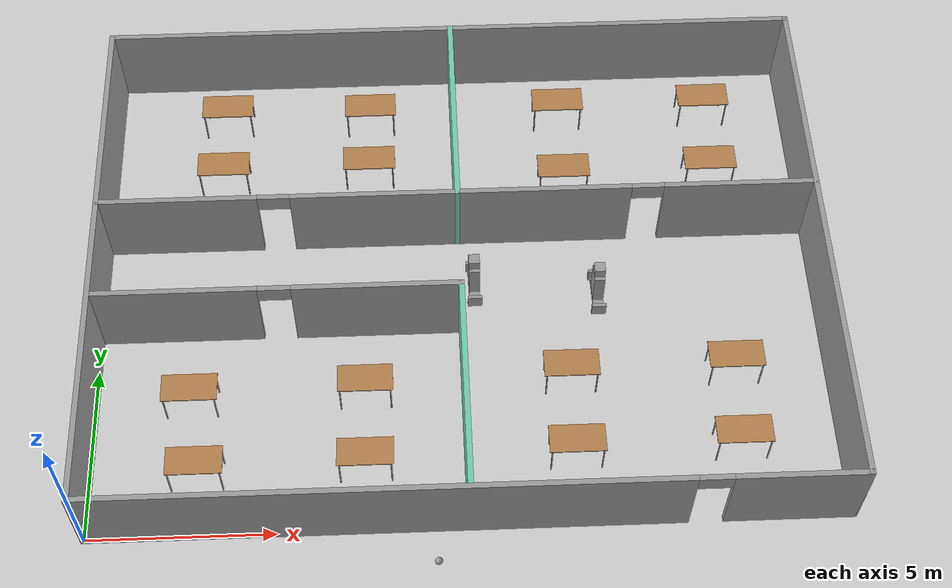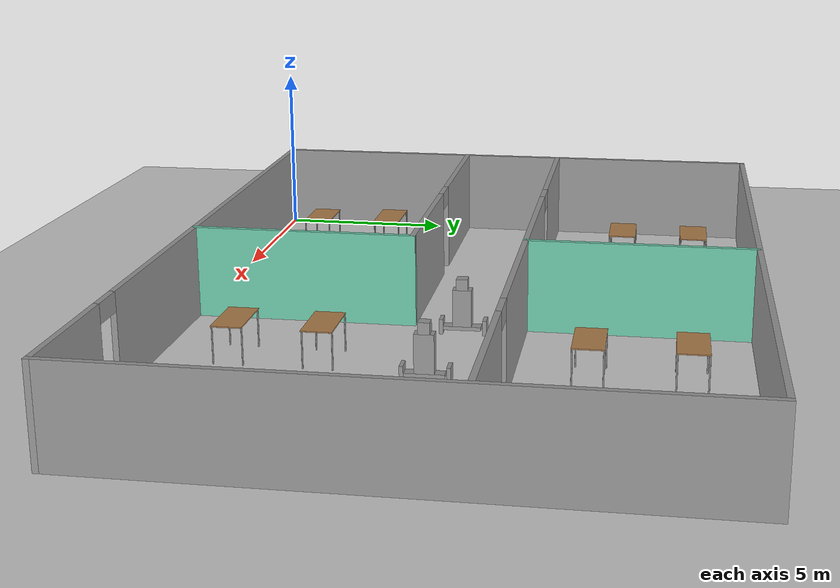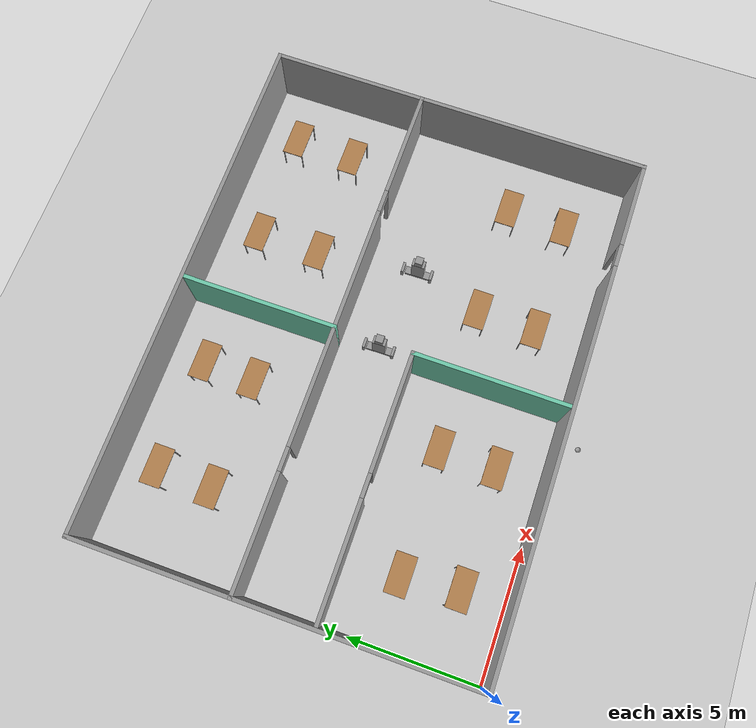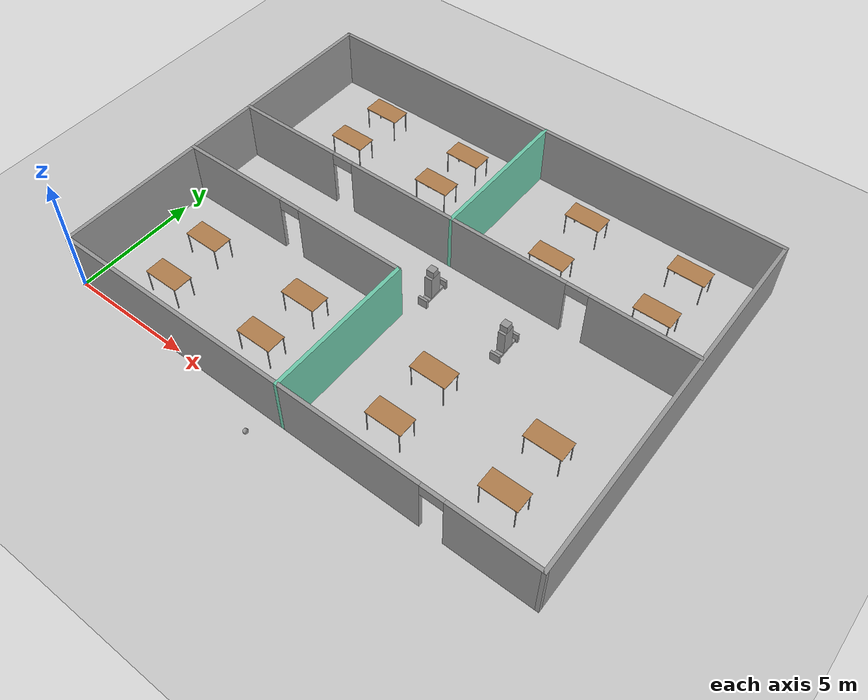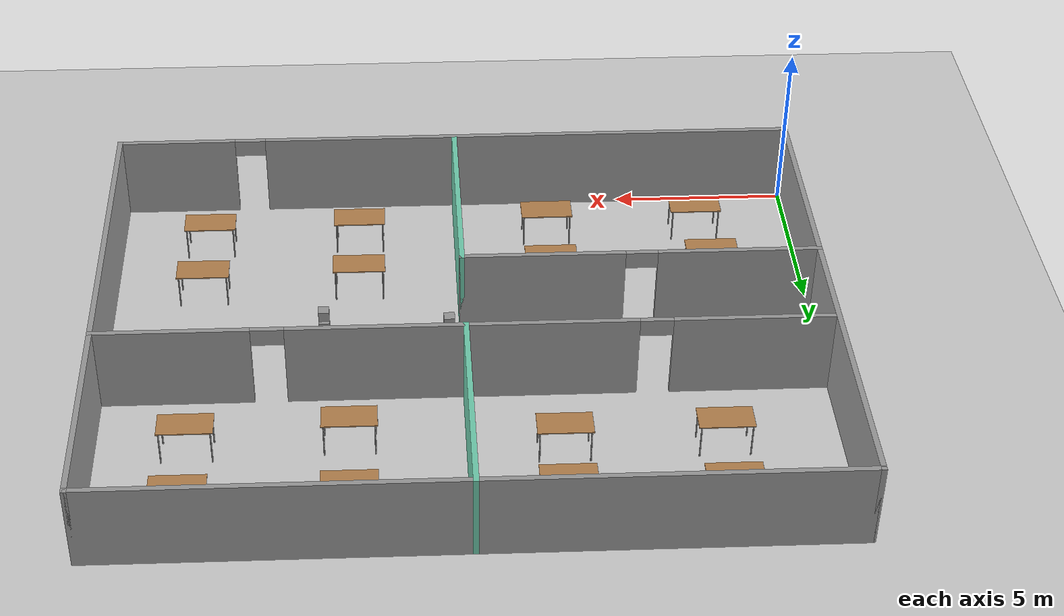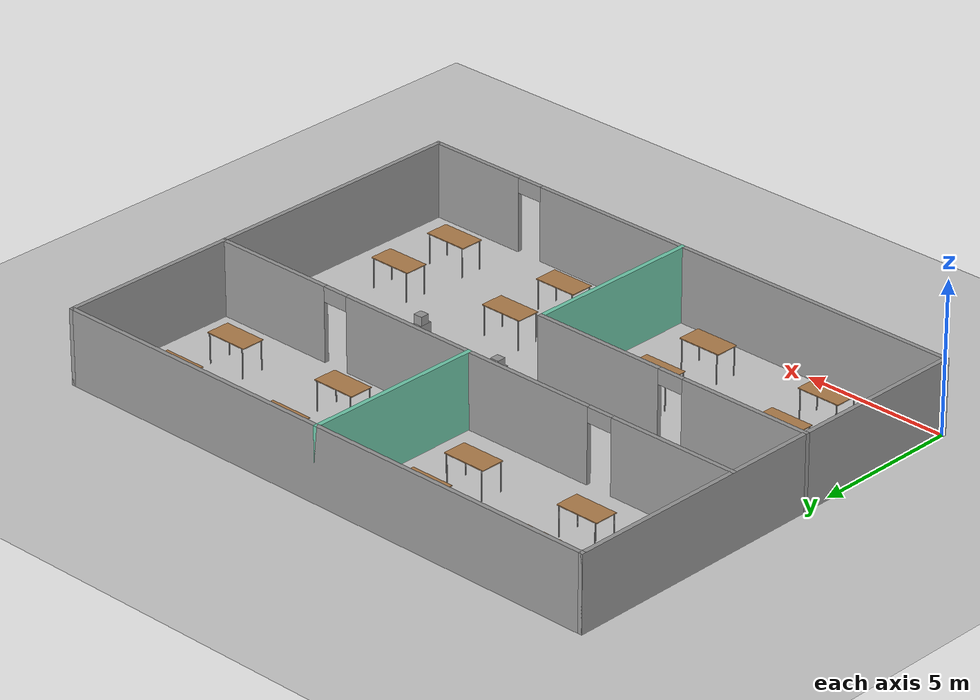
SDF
<sdf version="1.6">
 <world name="default">
  <plugin name="hello" filename="libhello.so"/>
  <light name="sun" type="directional">
   <pose>0 0 10 0 -0 0</pose>
   <diffuse>0.8 0.8 0.8 1</diffuse>
   <specular>0.2 0.2 0.2 1</specular>
   <attenuation>
    <range>1000</range>
    <constant>0.9</constant>
    <linear>0.01</linear>
    <quadratic>0.001</quadratic>
   </attenuation>
   <direction>-0.5 0.1 -0.9</direction>
  </light>
  <model name="ground_plane">
   <static>1</static>
   <link name="link">
    <collision name="collision">
     <geometry><plane><normal>0 0 1</normal><size>100 100</size></plane></geometry>
     <surface>
      <contact><collide_bitmask>65535</collide_bitmask></contact>
      <friction><ode><mu>100</mu><mu2>50</mu2></ode></friction>
     </surface>
    </collision>
    <visual name="visual">
     <cast_shadows>0</cast_shadows>
     <geometry><plane><normal>0 0 1</normal><size>100 100</size></plane></geometry>
     <material>
      <script><uri>file://media/materials/scripts/gazebo.material</uri><name>Gazebo/Grey</name></script>
     </material>
    </visual>
   </link>
  </model>
  <gravity>0 0 -9.8</gravity>
  <magnetic_field>6e-06 2.3e-05 -4.2e-05</magnetic_field>
  <atmosphere type="adiabatic"/>
  <physics name="default_physics" default="0" type="ode">
   <max_step_size>0.001</max_step_size>
   <real_time_factor>1</real_time_factor>
   <real_time_update_rate>1000</real_time_update_rate>
  </physics>
  <scene><ambient>0.4 0.4 0.4 1</ambient><background>0.7 0.7 0.7 1</background><shadows>1</shadows></scene>
  <spherical_coordinates>
   <surface_model>EARTH_WGS84</surface_model>
   <latitude_deg>0</latitude_deg>
   <longitude_deg>0</longitude_deg>
   <elevation>0</elevation>
   <heading_deg>0</heading_deg>
  </spherical_coordinates>
  <model name="mybuilding">
   <pose>10 7.5 0 0 -0 0</pose>
   <link name="Wall_11">
    <collision name="Wall_11_Collision">
     <geometry><box><size>15.15 0.15 2.5</size></box></geometry>
     <pose>0 0 1.25 0 -0 0</pose>
    </collision>
    <visual name="Wall_11_Visual">
     <pose>0 0 1.25 0 -0 0</pose>
     <geometry><box><size>15.15 0.15 2.5</size></box></geometry>
     <material>
      <script><uri>file://media/materials/scripts/gazebo.material</uri><name>Gazebo/Grey</name></script>
      <ambient>1 1 1 1</ambient>
     </material>
     <meta><layer>0</layer></meta>
    </visual>
    <pose>-10 0 0 0 -0 1.5708</pose>
   </link>
   <link name="Wall_13">
    <collision name="Wall_13_Collision">
     <geometry><box><size>20.15 0.15 2.5</size></box></geometry>
     <pose>0 0 1.25 0 -0 0</pose>
    </collision>
    <visual name="Wall_13_Visual">
     <pose>0 0 1.25 0 -0 0</pose>
     <geometry><box><size>20.15 0.15 2.5</size></box></geometry>
     <material>
      <script><uri>file://media/materials/scripts/gazebo.material</uri><name>Gazebo/Grey</name></script>
      <ambient>1 1 1 1</ambient>
     </material>
     <meta><layer>0</layer></meta>
    </visual>
    <pose>0 7.5 0 0 -0 0</pose>
   </link>
   <link name="Wall_15">
    <collision name="Wall_15_Collision">
     <geometry><box><size>15.15 0.15 2.5</size></box></geometry>
     <pose>0 0 1.25 0 -0 0</pose>
    </collision>
    <visual name="Wall_15_Visual">
     <pose>0 0 1.25 0 -0 0</pose>
     <geometry><box><size>15.15 0.15 2.5</size></box></geometry>
     <material>
      <script><uri>file://media/materials/scripts/gazebo.material</uri><name>Gazebo/Grey</name></script>
      <ambient>1 1 1 1</ambient>
     </material>
     <meta><layer>0</layer></meta>
    </visual>
    <pose>10 0 0 0 0 -1.5708</pose>
   </link>
   <link name="Wall_17">
    <pose>0 1.5 0 0 -0 0</pose>
    <visual name="Wall_17_Visual_0">
     <pose>-7.81586 0 1.25 0 -0 0</pose>
     <geometry><box><size>4.51827 0.15 2.5</size></box></geometry>
     <material>
      <script><uri>file://media/materials/scripts/gazebo.material</uri><name>Gazebo/Grey</name></script>
      <ambient>1 1 1 1</ambient>
     </material>
     <meta><layer>0</layer></meta>
    </visual>
    <collision name="Wall_17_Collision_0">
     <geometry><box><size>4.51827 0.15 2.5</size></box></geometry>
     <pose>-7.81586 0 1.25 0 -0 0</pose>
    </collision>
    <visual name="Wall_17_Visual_1">
     <pose>0.10099 0 1.25 0 -0 0</pose>
     <geometry><box><size>9.51544 0.15 2.5</size></box></geometry>
     <material>
      <script><uri>file://media/materials/scripts/gazebo.material</uri><name>Gazebo/Grey</name></script>
      <ambient>1 1 1 1</ambient>
     </material>
     <meta><layer>0</layer></meta>
    </visual>
    <collision name="Wall_17_Collision_1">
     <geometry><box><size>9.51544 0.15 2.5</size></box></geometry>
     <pose>0.10099 0 1.25 0 -0 0</pose>
    </collision>
    <visual name="Wall_17_Visual_2">
     <pose>7.91685 0 1.25 0 -0 0</pose>
     <geometry><box><size>4.31629 0.15 2.5</size></box></geometry>
     <material>
      <script><uri>file://media/materials/scripts/gazebo.material</uri><name>Gazebo/Grey</name></script>
      <ambient>1 1 1 1</ambient>
     </material>
     <meta><layer>0</layer></meta>
    </visual>
    <collision name="Wall_17_Collision_2">
     <geometry><box><size>4.31629 0.15 2.5</size></box></geometry>
     <pose>7.91685 0 1.25 0 -0 0</pose>
    </collision>
    <visual name="Wall_17_Visual_3">
     <pose>-5.10673 0 2.25 0 -0 0</pose>
     <geometry><box><size>0.9 0.15 0.5</size></box></geometry>
     <material>
      <script><uri>file://media/materials/scripts/gazebo.material</uri><name>Gazebo/Grey</name></script>
      <ambient>1 1 1 1</ambient>
     </material>
     <meta><layer>0</layer></meta>
    </visual>
    <collision name="Wall_17_Collision_3">
     <geometry><box><size>0.9 0.15 0.5</size></box></geometry>
     <pose>-5.10673 0 2.25 0 -0 0</pose>
    </collision>
    <visual name="Wall_17_Visual_4">
     <pose>5.30871 0 2.25 0 -0 0</pose>
     <geometry><box><size>0.9 0.15 0.5</size></box></geometry>
     <material>
      <script><uri>file://media/materials/scripts/gazebo.material</uri><name>Gazebo/Grey</name></script>
      <ambient>1 1 1 1</ambient>
     </material>
     <meta><layer>0</layer></meta>
    </visual>
    <collision name="Wall_17_Collision_4">
     <geometry><box><size>0.9 0.15 0.5</size></box></geometry>
     <pose>5.30871 0 2.25 0 -0 0</pose>
    </collision>
   </link>
   <link name="Wall_19">
    <collision name="Wall_19_Collision">
     <geometry><box><size>6.15 0.15 2.5</size></box></geometry>
     <pose>0 0 1.25 0 -0 0</pose>
    </collision>
    <visual name="Wall_19_Visual">
     <pose>0 0 1.25 0 -0 0</pose>
     <geometry><box><size>6.15 0.15 2.5</size></box></geometry>
     <material>
      <script><uri>file://media/materials/scripts/gazebo.material</uri><name>Gazebo/Grey</name></script>
      <ambient>0.435294 0.796078 0.67451 1</ambient>
     </material>
     <meta><layer>0</layer></meta>
    </visual>
    <pose>0 4.5 0 0 0 -1.5708</pose>
   </link>
   <link name="Wall_21">
    <pose>-5 -1.5 0 0 -0 0</pose>
    <visual name="Wall_21_Visual_0">
     <pose>-2.77518 0 1.25 0 -0 0</pose>
     <geometry><box><size>4.59964 0.15 2.5</size></box></geometry>
     <material>
      <script><uri>file://media/materials/scripts/gazebo.material</uri><name>Gazebo/Grey</name></script>
      <ambient>1 1 1 1</ambient>
     </material>
     <meta><layer>0</layer></meta>
    </visual>
    <collision name="Wall_21_Collision_0">
     <geometry><box><size>4.59964 0.15 2.5</size></box></geometry>
     <pose>-2.77518 0 1.25 0 -0 0</pose>
    </collision>
    <visual name="Wall_21_Visual_1">
     <pose>2.74982 0 1.25 0 -0 0</pose>
     <geometry><box><size>4.65036 0.15 2.5</size></box></geometry>
     <material>
      <script><uri>file://media/materials/scripts/gazebo.material</uri><name>Gazebo/Grey</name></script>
      <ambient>1 1 1 1</ambient>
     </material>
     <meta><layer>0</layer></meta>
    </visual>
    <collision name="Wall_21_Collision_1">
     <geometry><box><size>4.65036 0.15 2.5</size></box></geometry>
     <pose>2.74982 0 1.25 0 -0 0</pose>
    </collision>
    <visual name="Wall_21_Visual_2">
     <pose>-0.02536 0 2.25 0 -0 0</pose>
     <geometry><box><size>0.9 0.15 0.5</size></box></geometry>
     <material>
      <script><uri>file://media/materials/scripts/gazebo.material</uri><name>Gazebo/Grey</name></script>
      <ambient>1 1 1 1</ambient>
     </material>
     <meta><layer>0</layer></meta>
    </visual>
    <collision name="Wall_21_Collision_2">
     <geometry><box><size>0.9 0.15 0.5</size></box></geometry>
     <pose>-0.02536 0 2.25 0 -0 0</pose>
    </collision>
   </link>
   <link name="Wall_24">
    <collision name="Wall_24_Collision">
     <geometry><box><size>6.15 0.15 2.5</size></box></geometry>
     <pose>0 0 1.25 0 -0 0</pose>
    </collision>
    <visual name="Wall_24_Visual">
     <pose>0 0 1.25 0 -0 0</pose>
     <geometry><box><size>6.15 0.15 2.5</size></box></geometry>
     <material>
      <script><uri>file://media/materials/scripts/gazebo.material</uri><name>Gazebo/Grey</name></script>
      <ambient>0.435294 0.796078 0.67451 1</ambient>
     </material>
     <meta><layer>0</layer></meta>
    </visual>
    <pose>0 -4.5 0 0 0 -1.5708</pose>
   </link>
   <link name="Wall_9">
    <pose>0 -7.5 0 0 -0 0</pose>
    <visual name="Wall_9_Visual_0">
     <pose>-2.20129 0 1.25 0 -0 0</pose>
     <geometry><box><size>15.7474 0.15 2.5</size></box></geometry>
     <material>
      <script><uri>file://media/materials/scripts/gazebo.material</uri><name>Gazebo/Grey</name></script>
      <ambient>1 1 1 1</ambient>
     </material>
     <meta><layer>0</layer></meta>
    </visual>
    <collision name="Wall_9_Collision_0">
     <geometry><box><size>15.7474 0.15 2.5</size></box></geometry>
     <pose>-2.20129 0 1.25 0 -0 0</pose>
    </collision>
    <visual name="Wall_9_Visual_1">
     <pose>8.32371 0 1.25 0 -0 0</pose>
     <geometry><box><size>3.50258 0.15 2.5</size></box></geometry>
     <material>
      <script><uri>file://media/materials/scripts/gazebo.material</uri><name>Gazebo/Grey</name></script>
      <ambient>1 1 1 1</ambient>
     </material>
     <meta><layer>0</layer></meta>
    </visual>
    <collision name="Wall_9_Collision_1">
     <geometry><box><size>3.50258 0.15 2.5</size></box></geometry>
     <pose>8.32371 0 1.25 0 -0 0</pose>
    </collision>
    <visual name="Wall_9_Visual_2">
     <pose>6.12242 0 2.25 0 -0 0</pose>
     <geometry><box><size>0.9 0.15 0.5</size></box></geometry>
     <material>
      <script><uri>file://media/materials/scripts/gazebo.material</uri><name>Gazebo/Grey</name></script>
      <ambient>1 1 1 1</ambient>
     </material>
     <meta><layer>0</layer></meta>
    </visual>
    <collision name="Wall_9_Collision_2">
     <geometry><box><size>0.9 0.15 0.5</size></box></geometry>
     <pose>6.12242 0 2.25 0 -0 0</pose>
    </collision>
   </link>
   <static>1</static>
  </model>
  <model name="table">
   <static>1</static>
   <link name="link">
    <collision name="surface">
     <pose>0 0 1 0 -0 0</pose>
     <geometry><box><size>1.5 0.8 0.03</size></box></geometry>
     <surface><friction><ode><mu>0.6</mu><mu2>0.6</mu2></ode></friction></surface>
    </collision>
    <visual name="visual1">
     <pose>0 0 1 0 -0 0</pose>
     <geometry><box><size>1.5 0.8 0.03</size></box></geometry>
     <material>
      <script><uri>file://media/materials/scripts/gazebo.material</uri><name>Gazebo/Wood</name></script>
     </material>
    </visual>
    <collision name="front_left_leg">
     <pose>0.68 0.38 0.5 0 -0 0</pose>
     <geometry><cylinder><radius>0.02</radius><length>1</length></cylinder></geometry>
    </collision>
    <visual name="front_left_leg">
     <pose>0.68 0.38 0.5 0 -0 0</pose>
     <geometry><cylinder><radius>0.02</radius><length>1</length></cylinder></geometry>
     <material>
      <script><uri>file://media/materials/scripts/gazebo.material</uri><name>Gazebo/Grey</name></script>
     </material>
    </visual>
    <collision name="front_right_leg">
     <pose>0.68 -0.38 0.5 0 -0 0</pose>
     <geometry><cylinder><radius>0.02</radius><length>1</length></cylinder></geometry>
    </collision>
    <visual name="front_right_leg">
     <pose>0.68 -0.38 0.5 0 -0 0</pose>
     <geometry><cylinder><radius>0.02</radius><length>1</length></cylinder></geometry>
     <material>
      <script><uri>file://media/materials/scripts/gazebo.material</uri><name>Gazebo/Grey</name></script>
     </material>
    </visual>
    <collision name="back_right_leg">
     <pose>-0.68 -0.38 0.5 0 -0 0</pose>
     <geometry><cylinder><radius>0.02</radius><length>1</length></cylinder></geometry>
    </collision>
    <visual name="back_right_leg">
     <pose>-0.68 -0.38 0.5 0 -0 0</pose>
     <geometry><cylinder><radius>0.02</radius><length>1</length></cylinder></geometry>
     <material>
      <script><uri>file://media/materials/scripts/gazebo.material</uri><name>Gazebo/Grey</name></script>
     </material>
    </visual>
    <collision name="back_left_leg">
     <pose>-0.68 0.38 0.5 0 -0 0</pose>
     <geometry><cylinder><radius>0.02</radius><length>1</length></cylinder></geometry>
    </collision>
    <visual name="back_left_leg">
     <pose>-0.68 0.38 0.5 0 -0 0</pose>
     <geometry><cylinder><radius>0.02</radius><length>1</length></cylinder></geometry>
     <material>
      <script><uri>file://media/materials/scripts/gazebo.material</uri><name>Gazebo/Grey</name></script>
     </material>
    </visual>
   </link>
   <pose>17.3802 4.37607 0 0 -0 0</pose>
  </model>
  <model name="table_clone">
   <static>1</static>
   <link name="link">
    <collision name="surface">
     <pose>0 0 1 0 -0 0</pose>
     <geometry><box><size>1.5 0.8 0.03</size></box></geometry>
     <surface><friction><ode><mu>0.6</mu><mu2>0.6</mu2></ode></friction></surface>
    </collision>
    <visual name="visual1">
     <pose>0 0 1 0 -0 0</pose>
     <geometry><box><size>1.5 0.8 0.03</size></box></geometry>
     <material>
      <script><uri>file://media/materials/scripts/gazebo.material</uri><name>Gazebo/Wood</name></script>
     </material>
    </visual>
    <collision name="front_left_leg">
     <pose>0.68 0.38 0.5 0 -0 0</pose>
     <geometry><cylinder><radius>0.02</radius><length>1</length></cylinder></geometry>
    </collision>
    <visual name="front_left_leg">
     <pose>0.68 0.38 0.5 0 -0 0</pose>
     <geometry><cylinder><radius>0.02</radius><length>1</length></cylinder></geometry>
     <material>
      <script><uri>file://media/materials/scripts/gazebo.material</uri><name>Gazebo/Grey</name></script>
     </material>
    </visual>
    <collision name="front_right_leg">
     <pose>0.68 -0.38 0.5 0 -0 0</pose>
     <geometry><cylinder><radius>0.02</radius><length>1</length></cylinder></geometry>
    </collision>
    <visual name="front_right_leg">
     <pose>0.68 -0.38 0.5 0 -0 0</pose>
     <geometry><cylinder><radius>0.02</radius><length>1</length></cylinder></geometry>
     <material>
      <script><uri>file://media/materials/scripts/gazebo.material</uri><name>Gazebo/Grey</name></script>
     </material>
    </visual>
    <collision name="back_right_leg">
     <pose>-0.68 -0.38 0.5 0 -0 0</pose>
     <geometry><cylinder><radius>0.02</radius><length>1</length></cylinder></geometry>
    </collision>
    <visual name="back_right_leg">
     <pose>-0.68 -0.38 0.5 0 -0 0</pose>
     <geometry><cylinder><radius>0.02</radius><length>1</length></cylinder></geometry>
     <material>
      <script><uri>file://media/materials/scripts/gazebo.material</uri><name>Gazebo/Grey</name></script>
     </material>
    </visual>
    <collision name="back_left_leg">
     <pose>-0.68 0.38 0.5 0 -0 0</pose>
     <geometry><cylinder><radius>0.02</radius><length>1</length></cylinder></geometry>
    </collision>
    <visual name="back_left_leg">
     <pose>-0.68 0.38 0.5 0 -0 0</pose>
     <geometry><cylinder><radius>0.02</radius><length>1</length></cylinder></geometry>
     <material>
      <script><uri>file://media/materials/scripts/gazebo.material</uri><name>Gazebo/Grey</name></script>
     </material>
    </visual>
   </link>
   <pose>12.8854 1.98216 0 0 -0 0</pose>
  </model>
  <model name="table_clone_0">
   <static>1</static>
   <link name="link">
    <collision name="surface">
     <pose>0 0 1 0 -0 0</pose>
     <geometry><box><size>1.5 0.8 0.03</size></box></geometry>
     <surface><friction><ode><mu>0.6</mu><mu2>0.6</mu2></ode></friction></surface>
    </collision>
    <visual name="visual1">
     <pose>0 0 1 0 -0 0</pose>
     <geometry><box><size>1.5 0.8 0.03</size></box></geometry>
     <material>
      <script><uri>file://media/materials/scripts/gazebo.material</uri><name>Gazebo/Wood</name></script>
     </material>
    </visual>
    <collision name="front_left_leg">
     <pose>0.68 0.38 0.5 0 -0 0</pose>
     <geometry><cylinder><radius>0.02</radius><length>1</length></cylinder></geometry>
    </collision>
    <visual name="front_left_leg">
     <pose>0.68 0.38 0.5 0 -0 0</pose>
     <geometry><cylinder><radius>0.02</radius><length>1</length></cylinder></geometry>
     <material>
      <script><uri>file://media/materials/scripts/gazebo.material</uri><name>Gazebo/Grey</name></script>
     </material>
    </visual>
    <collision name="front_right_leg">
     <pose>0.68 -0.38 0.5 0 -0 0</pose>
     <geometry><cylinder><radius>0.02</radius><length>1</length></cylinder></geometry>
    </collision>
    <visual name="front_right_leg">
     <pose>0.68 -0.38 0.5 0 -0 0</pose>
     <geometry><cylinder><radius>0.02</radius><length>1</length></cylinder></geometry>
     <material>
      <script><uri>file://media/materials/scripts/gazebo.material</uri><name>Gazebo/Grey</name></script>
     </material>
    </visual>
    <collision name="back_right_leg">
     <pose>-0.68 -0.38 0.5 0 -0 0</pose>
     <geometry><cylinder><radius>0.02</radius><length>1</length></cylinder></geometry>
    </collision>
    <visual name="back_right_leg">
     <pose>-0.68 -0.38 0.5 0 -0 0</pose>
     <geometry><cylinder><radius>0.02</radius><length>1</length></cylinder></geometry>
     <material>
      <script><uri>file://media/materials/scripts/gazebo.material</uri><name>Gazebo/Grey</name></script>
     </material>
    </visual>
    <collision name="back_left_leg">
     <pose>-0.68 0.38 0.5 0 -0 0</pose>
     <geometry><cylinder><radius>0.02</radius><length>1</length></cylinder></geometry>
    </collision>
    <visual name="back_left_leg">
     <pose>-0.68 0.38 0.5 0 -0 0</pose>
     <geometry><cylinder><radius>0.02</radius><length>1</length></cylinder></geometry>
     <material>
      <script><uri>file://media/materials/scripts/gazebo.material</uri><name>Gazebo/Grey</name></script>
     </material>
    </visual>
   </link>
   <pose>12.9011 4.26699 0 0 -0 0</pose>
  </model>
  <model name="table_clone_1">
   <static>1</static>
   <link name="link">
    <collision name="surface">
     <pose>0 0 1 0 -0 0</pose>
     <geometry><box><size>1.5 0.8 0.03</size></box></geometry>
     <surface><friction><ode><mu>0.6</mu><mu2>0.6</mu2></ode></friction></surface>
    </collision>
    <visual name="visual1">
     <pose>0 0 1 0 -0 0</pose>
     <geometry><box><size>1.5 0.8 0.03</size></box></geometry>
     <material>
      <script><uri>file://media/materials/scripts/gazebo.material</uri><name>Gazebo/Wood</name></script>
     </material>
    </visual>
    <collision name="front_left_leg">
     <pose>0.68 0.38 0.5 0 -0 0</pose>
     <geometry><cylinder><radius>0.02</radius><length>1</length></cylinder></geometry>
    </collision>
    <visual name="front_left_leg">
     <pose>0.68 0.38 0.5 0 -0 0</pose>
     <geometry><cylinder><radius>0.02</radius><length>1</length></cylinder></geometry>
     <material>
      <script><uri>file://media/materials/scripts/gazebo.material</uri><name>Gazebo/Grey</name></script>
     </material>
    </visual>
    <collision name="front_right_leg">
     <pose>0.68 -0.38 0.5 0 -0 0</pose>
     <geometry><cylinder><radius>0.02</radius><length>1</length></cylinder></geometry>
    </collision>
    <visual name="front_right_leg">
     <pose>0.68 -0.38 0.5 0 -0 0</pose>
     <geometry><cylinder><radius>0.02</radius><length>1</length></cylinder></geometry>
     <material>
      <script><uri>file://media/materials/scripts/gazebo.material</uri><name>Gazebo/Grey</name></script>
     </material>
    </visual>
    <collision name="back_right_leg">
     <pose>-0.68 -0.38 0.5 0 -0 0</pose>
     <geometry><cylinder><radius>0.02</radius><length>1</length></cylinder></geometry>
    </collision>
    <visual name="back_right_leg">
     <pose>-0.68 -0.38 0.5 0 -0 0</pose>
     <geometry><cylinder><radius>0.02</radius><length>1</length></cylinder></geometry>
     <material>
      <script><uri>file://media/materials/scripts/gazebo.material</uri><name>Gazebo/Grey</name></script>
     </material>
    </visual>
    <collision name="back_left_leg">
     <pose>-0.68 0.38 0.5 0 -0 0</pose>
     <geometry><cylinder><radius>0.02</radius><length>1</length></cylinder></geometry>
    </collision>
    <visual name="back_left_leg">
     <pose>-0.68 0.38 0.5 0 -0 0</pose>
     <geometry><cylinder><radius>0.02</radius><length>1</length></cylinder></geometry>
     <material>
      <script><uri>file://media/materials/scripts/gazebo.material</uri><name>Gazebo/Grey</name></script>
     </material>
    </visual>
   </link>
   <pose>17.2977 2.08785 0 0 -0 0</pose>
  </model>
  <model name="table_0">
   <static>1</static>
   <link name="link">
    <collision name="surface">
     <pose>0 0 1 0 -0 0</pose>
     <geometry><box><size>1.5 0.8 0.03</size></box></geometry>
     <surface><friction><ode><mu>0.6</mu><mu2>0.6</mu2></ode></friction></surface>
    </collision>
    <visual name="visual1">
     <pose>0 0 1 0 -0 0</pose>
     <geometry><box><size>1.5 0.8 0.03</size></box></geometry>
     <material>
      <script><uri>file://media/materials/scripts/gazebo.material</uri><name>Gazebo/Wood</name></script>
     </material>
    </visual>
    <collision name="front_left_leg">
     <pose>0.68 0.38 0.5 0 -0 0</pose>
     <geometry><cylinder><radius>0.02</radius><length>1</length></cylinder></geometry>
    </collision>
    <visual name="front_left_leg">
     <pose>0.68 0.38 0.5 0 -0 0</pose>
     <geometry><cylinder><radius>0.02</radius><length>1</length></cylinder></geometry>
     <material>
      <script><uri>file://media/materials/scripts/gazebo.material</uri><name>Gazebo/Grey</name></script>
     </material>
    </visual>
    <collision name="front_right_leg">
     <pose>0.68 -0.38 0.5 0 -0 0</pose>
     <geometry><cylinder><radius>0.02</radius><length>1</length></cylinder></geometry>
    </collision>
    <visual name="front_right_leg">
     <pose>0.68 -0.38 0.5 0 -0 0</pose>
     <geometry><cylinder><radius>0.02</radius><length>1</length></cylinder></geometry>
     <material>
      <script><uri>file://media/materials/scripts/gazebo.material</uri><name>Gazebo/Grey</name></script>
     </material>
    </visual>
    <collision name="back_right_leg">
     <pose>-0.68 -0.38 0.5 0 -0 0</pose>
     <geometry><cylinder><radius>0.02</radius><length>1</length></cylinder></geometry>
    </collision>
    <visual name="back_right_leg">
     <pose>-0.68 -0.38 0.5 0 -0 0</pose>
     <geometry><cylinder><radius>0.02</radius><length>1</length></cylinder></geometry>
     <material>
      <script><uri>file://media/materials/scripts/gazebo.material</uri><name>Gazebo/Grey</name></script>
     </material>
    </visual>
    <collision name="back_left_leg">
     <pose>-0.68 0.38 0.5 0 -0 0</pose>
     <geometry><cylinder><radius>0.02</radius><length>1</length></cylinder></geometry>
    </collision>
    <visual name="back_left_leg">
     <pose>-0.68 0.38 0.5 0 -0 0</pose>
     <geometry><cylinder><radius>0.02</radius><length>1</length></cylinder></geometry>
     <material>
      <script><uri>file://media/materials/scripts/gazebo.material</uri><name>Gazebo/Grey</name></script>
     </material>
    </visual>
   </link>
   <pose>7.55328 13.3497 0 0 -0 0</pose>
  </model>
  <model name="table_clone_2">
   <static>1</static>
   <link name="link">
    <collision name="surface">
     <pose>0 0 1 0 -0 0</pose>
     <geometry><box><size>1.5 0.8 0.03</size></box></geometry>
     <surface><friction><ode><mu>0.6</mu><mu2>0.6</mu2></ode></friction></surface>
    </collision>
    <visual name="visual1">
     <pose>0 0 1 0 -0 0</pose>
     <geometry><box><size>1.5 0.8 0.03</size></box></geometry>
     <material>
      <script><uri>file://media/materials/scripts/gazebo.material</uri><name>Gazebo/Wood</name></script>
     </material>
    </visual>
    <collision name="front_left_leg">
     <pose>0.68 0.38 0.5 0 -0 0</pose>
     <geometry><cylinder><radius>0.02</radius><length>1</length></cylinder></geometry>
    </collision>
    <visual name="front_left_leg">
     <pose>0.68 0.38 0.5 0 -0 0</pose>
     <geometry><cylinder><radius>0.02</radius><length>1</length></cylinder></geometry>
     <material>
      <script><uri>file://media/materials/scripts/gazebo.material</uri><name>Gazebo/Grey</name></script>
     </material>
    </visual>
    <collision name="front_right_leg">
     <pose>0.68 -0.38 0.5 0 -0 0</pose>
     <geometry><cylinder><radius>0.02</radius><length>1</length></cylinder></geometry>
    </collision>
    <visual name="front_right_leg">
     <pose>0.68 -0.38 0.5 0 -0 0</pose>
     <geometry><cylinder><radius>0.02</radius><length>1</length></cylinder></geometry>
     <material>
      <script><uri>file://media/materials/scripts/gazebo.material</uri><name>Gazebo/Grey</name></script>
     </material>
    </visual>
    <collision name="back_right_leg">
     <pose>-0.68 -0.38 0.5 0 -0 0</pose>
     <geometry><cylinder><radius>0.02</radius><length>1</length></cylinder></geometry>
    </collision>
    <visual name="back_right_leg">
     <pose>-0.68 -0.38 0.5 0 -0 0</pose>
     <geometry><cylinder><radius>0.02</radius><length>1</length></cylinder></geometry>
     <material>
      <script><uri>file://media/materials/scripts/gazebo.material</uri><name>Gazebo/Grey</name></script>
     </material>
    </visual>
    <collision name="back_left_leg">
     <pose>-0.68 0.38 0.5 0 -0 0</pose>
     <geometry><cylinder><radius>0.02</radius><length>1</length></cylinder></geometry>
    </collision>
    <visual name="back_left_leg">
     <pose>-0.68 0.38 0.5 0 -0 0</pose>
     <geometry><cylinder><radius>0.02</radius><length>1</length></cylinder></geometry>
     <material>
      <script><uri>file://media/materials/scripts/gazebo.material</uri><name>Gazebo/Grey</name></script>
     </material>
    </visual>
   </link>
   <pose>3.3068 13.4619 0 0 -0 0</pose>
  </model>
  <model name="table_1">
   <static>1</static>
   <link name="link">
    <collision name="surface">
     <pose>0 0 1 0 -0 0</pose>
     <geometry><box><size>1.5 0.8 0.03</size></box></geometry>
     <surface><friction><ode><mu>0.6</mu><mu2>0.6</mu2></ode></friction></surface>
    </collision>
    <visual name="visual1">
     <pose>0 0 1 0 -0 0</pose>
     <geometry><box><size>1.5 0.8 0.03</size></box></geometry>
     <material>
      <script><uri>file://media/materials/scripts/gazebo.material</uri><name>Gazebo/Wood</name></script>
     </material>
    </visual>
    <collision name="front_left_leg">
     <pose>0.68 0.38 0.5 0 -0 0</pose>
     <geometry><cylinder><radius>0.02</radius><length>1</length></cylinder></geometry>
    </collision>
    <visual name="front_left_leg">
     <pose>0.68 0.38 0.5 0 -0 0</pose>
     <geometry><cylinder><radius>0.02</radius><length>1</length></cylinder></geometry>
     <material>
      <script><uri>file://media/materials/scripts/gazebo.material</uri><name>Gazebo/Grey</name></script>
     </material>
    </visual>
    <collision name="front_right_leg">
     <pose>0.68 -0.38 0.5 0 -0 0</pose>
     <geometry><cylinder><radius>0.02</radius><length>1</length></cylinder></geometry>
    </collision>
    <visual name="front_right_leg">
     <pose>0.68 -0.38 0.5 0 -0 0</pose>
     <geometry><cylinder><radius>0.02</radius><length>1</length></cylinder></geometry>
     <material>
      <script><uri>file://media/materials/scripts/gazebo.material</uri><name>Gazebo/Grey</name></script>
     </material>
    </visual>
    <collision name="back_right_leg">
     <pose>-0.68 -0.38 0.5 0 -0 0</pose>
     <geometry><cylinder><radius>0.02</radius><length>1</length></cylinder></geometry>
    </collision>
    <visual name="back_right_leg">
     <pose>-0.68 -0.38 0.5 0 -0 0</pose>
     <geometry><cylinder><radius>0.02</radius><length>1</length></cylinder></geometry>
     <material>
      <script><uri>file://media/materials/scripts/gazebo.material</uri><name>Gazebo/Grey</name></script>
     </material>
    </visual>
    <collision name="back_left_leg">
     <pose>-0.68 0.38 0.5 0 -0 0</pose>
     <geometry><cylinder><radius>0.02</radius><length>1</length></cylinder></geometry>
    </collision>
    <visual name="back_left_leg">
     <pose>-0.68 0.38 0.5 0 -0 0</pose>
     <geometry><cylinder><radius>0.02</radius><length>1</length></cylinder></geometry>
     <material>
      <script><uri>file://media/materials/scripts/gazebo.material</uri><name>Gazebo/Grey</name></script>
     </material>
    </visual>
   </link>
   <pose>17.504 13.3719 0 0 -0 0</pose>
  </model>
  <model name="table_2">
   <static>1</static>
   <link name="link">
    <collision name="surface">
     <pose>0 0 1 0 -0 0</pose>
     <geometry><box><size>1.5 0.8 0.03</size></box></geometry>
     <surface><friction><ode><mu>0.6</mu><mu2>0.6</mu2></ode></friction></surface>
    </collision>
    <visual name="visual1">
     <pose>0 0 1 0 -0 0</pose>
     <geometry><box><size>1.5 0.8 0.03</size></box></geometry>
     <material>
      <script><uri>file://media/materials/scripts/gazebo.material</uri><name>Gazebo/Wood</name></script>
     </material>
    </visual>
    <collision name="front_left_leg">
     <pose>0.68 0.38 0.5 0 -0 0</pose>
     <geometry><cylinder><radius>0.02</radius><length>1</length></cylinder></geometry>
    </collision>
    <visual name="front_left_leg">
     <pose>0.68 0.38 0.5 0 -0 0</pose>
     <geometry><cylinder><radius>0.02</radius><length>1</length></cylinder></geometry>
     <material>
      <script><uri>file://media/materials/scripts/gazebo.material</uri><name>Gazebo/Grey</name></script>
     </material>
    </visual>
    <collision name="front_right_leg">
     <pose>0.68 -0.38 0.5 0 -0 0</pose>
     <geometry><cylinder><radius>0.02</radius><length>1</length></cylinder></geometry>
    </collision>
    <visual name="front_right_leg">
     <pose>0.68 -0.38 0.5 0 -0 0</pose>
     <geometry><cylinder><radius>0.02</radius><length>1</length></cylinder></geometry>
     <material>
      <script><uri>file://media/materials/scripts/gazebo.material</uri><name>Gazebo/Grey</name></script>
     </material>
    </visual>
    <collision name="back_right_leg">
     <pose>-0.68 -0.38 0.5 0 -0 0</pose>
     <geometry><cylinder><radius>0.02</radius><length>1</length></cylinder></geometry>
    </collision>
    <visual name="back_right_leg">
     <pose>-0.68 -0.38 0.5 0 -0 0</pose>
     <geometry><cylinder><radius>0.02</radius><length>1</length></cylinder></geometry>
     <material>
      <script><uri>file://media/materials/scripts/gazebo.material</uri><name>Gazebo/Grey</name></script>
     </material>
    </visual>
    <collision name="back_left_leg">
     <pose>-0.68 0.38 0.5 0 -0 0</pose>
     <geometry><cylinder><radius>0.02</radius><length>1</length></cylinder></geometry>
    </collision>
    <visual name="back_left_leg">
     <pose>-0.68 0.38 0.5 0 -0 0</pose>
     <geometry><cylinder><radius>0.02</radius><length>1</length></cylinder></geometry>
     <material>
      <script><uri>file://media/materials/scripts/gazebo.material</uri><name>Gazebo/Grey</name></script>
     </material>
    </visual>
   </link>
   <pose>13.1412 13.36 0 0 -0 0</pose>
  </model>
  <model name="table_3">
   <static>1</static>
   <link name="link">
    <collision name="surface">
     <pose>0 0 1 0 -0 0</pose>
     <geometry><box><size>1.5 0.8 0.03</size></box></geometry>
     <surface><friction><ode><mu>0.6</mu><mu2>0.6</mu2></ode></friction></surface>
    </collision>
    <visual name="visual1">
     <pose>0 0 1 0 -0 0</pose>
     <geometry><box><size>1.5 0.8 0.03</size></box></geometry>
     <material>
      <script><uri>file://media/materials/scripts/gazebo.material</uri><name>Gazebo/Wood</name></script>
     </material>
    </visual>
    <collision name="front_left_leg">
     <pose>0.68 0.38 0.5 0 -0 0</pose>
     <geometry><cylinder><radius>0.02</radius><length>1</length></cylinder></geometry>
    </collision>
    <visual name="front_left_leg">
     <pose>0.68 0.38 0.5 0 -0 0</pose>
     <geometry><cylinder><radius>0.02</radius><length>1</length></cylinder></geometry>
     <material>
      <script><uri>file://media/materials/scripts/gazebo.material</uri><name>Gazebo/Grey</name></script>
     </material>
    </visual>
    <collision name="front_right_leg">
     <pose>0.68 -0.38 0.5 0 -0 0</pose>
     <geometry><cylinder><radius>0.02</radius><length>1</length></cylinder></geometry>
    </collision>
    <visual name="front_right_leg">
     <pose>0.68 -0.38 0.5 0 -0 0</pose>
     <geometry><cylinder><radius>0.02</radius><length>1</length></cylinder></geometry>
     <material>
      <script><uri>file://media/materials/scripts/gazebo.material</uri><name>Gazebo/Grey</name></script>
     </material>
    </visual>
    <collision name="back_right_leg">
     <pose>-0.68 -0.38 0.5 0 -0 0</pose>
     <geometry><cylinder><radius>0.02</radius><length>1</length></cylinder></geometry>
    </collision>
    <visual name="back_right_leg">
     <pose>-0.68 -0.38 0.5 0 -0 0</pose>
     <geometry><cylinder><radius>0.02</radius><length>1</length></cylinder></geometry>
     <material>
      <script><uri>file://media/materials/scripts/gazebo.material</uri><name>Gazebo/Grey</name></script>
     </material>
    </visual>
    <collision name="back_left_leg">
     <pose>-0.68 0.38 0.5 0 -0 0</pose>
     <geometry><cylinder><radius>0.02</radius><length>1</length></cylinder></geometry>
    </collision>
    <visual name="back_left_leg">
     <pose>-0.68 0.38 0.5 0 -0 0</pose>
     <geometry><cylinder><radius>0.02</radius><length>1</length></cylinder></geometry>
     <material>
      <script><uri>file://media/materials/scripts/gazebo.material</uri><name>Gazebo/Grey</name></script>
     </material>
    </visual>
   </link>
   <pose>7.33008 4.00792 0 0 -0 0</pose>
  </model>
  <model name="table_4">
   <static>1</static>
   <link name="link">
    <collision name="surface">
     <pose>0 0 1 0 -0 0</pose>
     <geometry><box><size>1.5 0.8 0.03</size></box></geometry>
     <surface><friction><ode><mu>0.6</mu><mu2>0.6</mu2></ode></friction></surface>
    </collision>
    <visual name="visual1">
     <pose>0 0 1 0 -0 0</pose>
     <geometry><box><size>1.5 0.8 0.03</size></box></geometry>
     <material>
      <script><uri>file://media/materials/scripts/gazebo.material</uri><name>Gazebo/Wood</name></script>
     </material>
    </visual>
    <collision name="front_left_leg">
     <pose>0.68 0.38 0.5 0 -0 0</pose>
     <geometry><cylinder><radius>0.02</radius><length>1</length></cylinder></geometry>
    </collision>
    <visual name="front_left_leg">
     <pose>0.68 0.38 0.5 0 -0 0</pose>
     <geometry><cylinder><radius>0.02</radius><length>1</length></cylinder></geometry>
     <material>
      <script><uri>file://media/materials/scripts/gazebo.material</uri><name>Gazebo/Grey</name></script>
     </material>
    </visual>
    <collision name="front_right_leg">
     <pose>0.68 -0.38 0.5 0 -0 0</pose>
     <geometry><cylinder><radius>0.02</radius><length>1</length></cylinder></geometry>
    </collision>
    <visual name="front_right_leg">
     <pose>0.68 -0.38 0.5 0 -0 0</pose>
     <geometry><cylinder><radius>0.02</radius><length>1</length></cylinder></geometry>
     <material>
      <script><uri>file://media/materials/scripts/gazebo.material</uri><name>Gazebo/Grey</name></script>
     </material>
    </visual>
    <collision name="back_right_leg">
     <pose>-0.68 -0.38 0.5 0 -0 0</pose>
     <geometry><cylinder><radius>0.02</radius><length>1</length></cylinder></geometry>
    </collision>
    <visual name="back_right_leg">
     <pose>-0.68 -0.38 0.5 0 -0 0</pose>
     <geometry><cylinder><radius>0.02</radius><length>1</length></cylinder></geometry>
     <material>
      <script><uri>file://media/materials/scripts/gazebo.material</uri><name>Gazebo/Grey</name></script>
     </material>
    </visual>
    <collision name="back_left_leg">
     <pose>-0.68 0.38 0.5 0 -0 0</pose>
     <geometry><cylinder><radius>0.02</radius><length>1</length></cylinder></geometry>
    </collision>
    <visual name="back_left_leg">
     <pose>-0.68 0.38 0.5 0 -0 0</pose>
     <geometry><cylinder><radius>0.02</radius><length>1</length></cylinder></geometry>
     <material>
      <script><uri>file://media/materials/scripts/gazebo.material</uri><name>Gazebo/Grey</name></script>
     </material>
    </visual>
   </link>
   <pose>2.63408 3.89107 0 0 -0 0</pose>
  </model>
  <model name="table_clone_3">
   <static>1</static>
   <link name="link">
    <collision name="surface">
     <pose>0 0 1 0 -0 0</pose>
     <geometry><box><size>1.5 0.8 0.03</size></box></geometry>
     <surface><friction><ode><mu>0.6</mu><mu2>0.6</mu2></ode></friction></surface>
    </collision>
    <visual name="visual1">
     <pose>0 0 1 0 -0 0</pose>
     <geometry><box><size>1.5 0.8 0.03</size></box></geometry>
     <material>
      <script><uri>file://media/materials/scripts/gazebo.material</uri><name>Gazebo/Wood</name></script>
     </material>
    </visual>
    <collision name="front_left_leg">
     <pose>0.68 0.38 0.5 0 -0 0</pose>
     <geometry><cylinder><radius>0.02</radius><length>1</length></cylinder></geometry>
    </collision>
    <visual name="front_left_leg">
     <pose>0.68 0.38 0.5 0 -0 0</pose>
     <geometry><cylinder><radius>0.02</radius><length>1</length></cylinder></geometry>
     <material>
      <script><uri>file://media/materials/scripts/gazebo.material</uri><name>Gazebo/Grey</name></script>
     </material>
    </visual>
    <collision name="front_right_leg">
     <pose>0.68 -0.38 0.5 0 -0 0</pose>
     <geometry><cylinder><radius>0.02</radius><length>1</length></cylinder></geometry>
    </collision>
    <visual name="front_right_leg">
     <pose>0.68 -0.38 0.5 0 -0 0</pose>
     <geometry><cylinder><radius>0.02</radius><length>1</length></cylinder></geometry>
     <material>
      <script><uri>file://media/materials/scripts/gazebo.material</uri><name>Gazebo/Grey</name></script>
     </material>
    </visual>
    <collision name="back_right_leg">
     <pose>-0.68 -0.38 0.5 0 -0 0</pose>
     <geometry><cylinder><radius>0.02</radius><length>1</length></cylinder></geometry>
    </collision>
    <visual name="back_right_leg">
     <pose>-0.68 -0.38 0.5 0 -0 0</pose>
     <geometry><cylinder><radius>0.02</radius><length>1</length></cylinder></geometry>
     <material>
      <script><uri>file://media/materials/scripts/gazebo.material</uri><name>Gazebo/Grey</name></script>
     </material>
    </visual>
    <collision name="back_left_leg">
     <pose>-0.68 0.38 0.5 0 -0 0</pose>
     <geometry><cylinder><radius>0.02</radius><length>1</length></cylinder></geometry>
    </collision>
    <visual name="back_left_leg">
     <pose>-0.68 0.38 0.5 0 -0 0</pose>
     <geometry><cylinder><radius>0.02</radius><length>1</length></cylinder></geometry>
     <material>
      <script><uri>file://media/materials/scripts/gazebo.material</uri><name>Gazebo/Grey</name></script>
     </material>
    </visual>
   </link>
   <pose>7.50168 11.381 0 0 -0 0</pose>
  </model>
  <model name="table_clone_4">
   <static>1</static>
   <link name="link">
    <collision name="surface">
     <pose>0 0 1 0 -0 0</pose>
     <geometry><box><size>1.5 0.8 0.03</size></box></geometry>
     <surface><friction><ode><mu>0.6</mu><mu2>0.6</mu2></ode></friction></surface>
    </collision>
    <visual name="visual1">
     <pose>0 0 1 0 -0 0</pose>
     <geometry><box><size>1.5 0.8 0.03</size></box></geometry>
     <material>
      <script><uri>file://media/materials/scripts/gazebo.material</uri><name>Gazebo/Wood</name></script>
     </material>
    </visual>
    <collision name="front_left_leg">
     <pose>0.68 0.38 0.5 0 -0 0</pose>
     <geometry><cylinder><radius>0.02</radius><length>1</length></cylinder></geometry>
    </collision>
    <visual name="front_left_leg">
     <pose>0.68 0.38 0.5 0 -0 0</pose>
     <geometry><cylinder><radius>0.02</radius><length>1</length></cylinder></geometry>
     <material>
      <script><uri>file://media/materials/scripts/gazebo.material</uri><name>Gazebo/Grey</name></script>
     </material>
    </visual>
    <collision name="front_right_leg">
     <pose>0.68 -0.38 0.5 0 -0 0</pose>
     <geometry><cylinder><radius>0.02</radius><length>1</length></cylinder></geometry>
    </collision>
    <visual name="front_right_leg">
     <pose>0.68 -0.38 0.5 0 -0 0</pose>
     <geometry><cylinder><radius>0.02</radius><length>1</length></cylinder></geometry>
     <material>
      <script><uri>file://media/materials/scripts/gazebo.material</uri><name>Gazebo/Grey</name></script>
     </material>
    </visual>
    <collision name="back_right_leg">
     <pose>-0.68 -0.38 0.5 0 -0 0</pose>
     <geometry><cylinder><radius>0.02</radius><length>1</length></cylinder></geometry>
    </collision>
    <visual name="back_right_leg">
     <pose>-0.68 -0.38 0.5 0 -0 0</pose>
     <geometry><cylinder><radius>0.02</radius><length>1</length></cylinder></geometry>
     <material>
      <script><uri>file://media/materials/scripts/gazebo.material</uri><name>Gazebo/Grey</name></script>
     </material>
    </visual>
    <collision name="back_left_leg">
     <pose>-0.68 0.38 0.5 0 -0 0</pose>
     <geometry><cylinder><radius>0.02</radius><length>1</length></cylinder></geometry>
    </collision>
    <visual name="back_left_leg">
     <pose>-0.68 0.38 0.5 0 -0 0</pose>
     <geometry><cylinder><radius>0.02</radius><length>1</length></cylinder></geometry>
     <material>
      <script><uri>file://media/materials/scripts/gazebo.material</uri><name>Gazebo/Grey</name></script>
     </material>
    </visual>
   </link>
   <pose>3.25865 11.3215 0 0 -0 0</pose>
  </model>
  <model name="table_clone_5">
   <static>1</static>
   <link name="link">
    <collision name="surface">
     <pose>0 0 1 0 -0 0</pose>
     <geometry><box><size>1.5 0.8 0.03</size></box></geometry>
     <surface><friction><ode><mu>0.6</mu><mu2>0.6</mu2></ode></friction></surface>
    </collision>
    <visual name="visual1">
     <pose>0 0 1 0 -0 0</pose>
     <geometry><box><size>1.5 0.8 0.03</size></box></geometry>
     <material>
      <script><uri>file://media/materials/scripts/gazebo.material</uri><name>Gazebo/Wood</name></script>
     </material>
    </visual>
    <collision name="front_left_leg">
     <pose>0.68 0.38 0.5 0 -0 0</pose>
     <geometry><cylinder><radius>0.02</radius><length>1</length></cylinder></geometry>
    </collision>
    <visual name="front_left_leg">
     <pose>0.68 0.38 0.5 0 -0 0</pose>
     <geometry><cylinder><radius>0.02</radius><length>1</length></cylinder></geometry>
     <material>
      <script><uri>file://media/materials/scripts/gazebo.material</uri><name>Gazebo/Grey</name></script>
     </material>
    </visual>
    <collision name="front_right_leg">
     <pose>0.68 -0.38 0.5 0 -0 0</pose>
     <geometry><cylinder><radius>0.02</radius><length>1</length></cylinder></geometry>
    </collision>
    <visual name="front_right_leg">
     <pose>0.68 -0.38 0.5 0 -0 0</pose>
     <geometry><cylinder><radius>0.02</radius><length>1</length></cylinder></geometry>
     <material>
      <script><uri>file://media/materials/scripts/gazebo.material</uri><name>Gazebo/Grey</name></script>
     </material>
    </visual>
    <collision name="back_right_leg">
     <pose>-0.68 -0.38 0.5 0 -0 0</pose>
     <geometry><cylinder><radius>0.02</radius><length>1</length></cylinder></geometry>
    </collision>
    <visual name="back_right_leg">
     <pose>-0.68 -0.38 0.5 0 -0 0</pose>
     <geometry><cylinder><radius>0.02</radius><length>1</length></cylinder></geometry>
     <material>
      <script><uri>file://media/materials/scripts/gazebo.material</uri><name>Gazebo/Grey</name></script>
     </material>
    </visual>
    <collision name="back_left_leg">
     <pose>-0.68 0.38 0.5 0 -0 0</pose>
     <geometry><cylinder><radius>0.02</radius><length>1</length></cylinder></geometry>
    </collision>
    <visual name="back_left_leg">
     <pose>-0.68 0.38 0.5 0 -0 0</pose>
     <geometry><cylinder><radius>0.02</radius><length>1</length></cylinder></geometry>
     <material>
      <script><uri>file://media/materials/scripts/gazebo.material</uri><name>Gazebo/Grey</name></script>
     </material>
    </visual>
   </link>
   <pose>7.31912 1.80991 0 0 -0 0</pose>
  </model>
  <model name="table_clone_6">
   <static>1</static>
   <link name="link">
    <collision name="surface">
     <pose>0 0 1 0 -0 0</pose>
     <geometry><box><size>1.5 0.8 0.03</size></box></geometry>
     <surface><friction><ode><mu>0.6</mu><mu2>0.6</mu2></ode></friction></surface>
    </collision>
    <visual name="visual1">
     <pose>0 0 1 0 -0 0</pose>
     <geometry><box><size>1.5 0.8 0.03</size></box></geometry>
     <material>
      <script><uri>file://media/materials/scripts/gazebo.material</uri><name>Gazebo/Wood</name></script>
     </material>
    </visual>
    <collision name="front_left_leg">
     <pose>0.68 0.38 0.5 0 -0 0</pose>
     <geometry><cylinder><radius>0.02</radius><length>1</length></cylinder></geometry>
    </collision>
    <visual name="front_left_leg">
     <pose>0.68 0.38 0.5 0 -0 0</pose>
     <geometry><cylinder><radius>0.02</radius><length>1</length></cylinder></geometry>
     <material>
      <script><uri>file://media/materials/scripts/gazebo.material</uri><name>Gazebo/Grey</name></script>
     </material>
    </visual>
    <collision name="front_right_leg">
     <pose>0.68 -0.38 0.5 0 -0 0</pose>
     <geometry><cylinder><radius>0.02</radius><length>1</length></cylinder></geometry>
    </collision>
    <visual name="front_right_leg">
     <pose>0.68 -0.38 0.5 0 -0 0</pose>
     <geometry><cylinder><radius>0.02</radius><length>1</length></cylinder></geometry>
     <material>
      <script><uri>file://media/materials/scripts/gazebo.material</uri><name>Gazebo/Grey</name></script>
     </material>
    </visual>
    <collision name="back_right_leg">
     <pose>-0.68 -0.38 0.5 0 -0 0</pose>
     <geometry><cylinder><radius>0.02</radius><length>1</length></cylinder></geometry>
    </collision>
    <visual name="back_right_leg">
     <pose>-0.68 -0.38 0.5 0 -0 0</pose>
     <geometry><cylinder><radius>0.02</radius><length>1</length></cylinder></geometry>
     <material>
      <script><uri>file://media/materials/scripts/gazebo.material</uri><name>Gazebo/Grey</name></script>
     </material>
    </visual>
    <collision name="back_left_leg">
     <pose>-0.68 0.38 0.5 0 -0 0</pose>
     <geometry><cylinder><radius>0.02</radius><length>1</length></cylinder></geometry>
    </collision>
    <visual name="back_left_leg">
     <pose>-0.68 0.38 0.5 0 -0 0</pose>
     <geometry><cylinder><radius>0.02</radius><length>1</length></cylinder></geometry>
     <material>
      <script><uri>file://media/materials/scripts/gazebo.material</uri><name>Gazebo/Grey</name></script>
     </material>
    </visual>
   </link>
   <pose>2.86362 1.71508 0 0 -0 0</pose>
  </model>
  <model name="table_clone_7">
   <static>1</static>
   <link name="link">
    <collision name="surface">
     <pose>0 0 1 0 -0 0</pose>
     <geometry><box><size>1.5 0.8 0.03</size></box></geometry>
     <surface><friction><ode><mu>0.6</mu><mu2>0.6</mu2></ode></friction></surface>
    </collision>
    <visual name="visual1">
     <pose>0 0 1 0 -0 0</pose>
     <geometry><box><size>1.5 0.8 0.03</size></box></geometry>
     <material>
      <script><uri>file://media/materials/scripts/gazebo.material</uri><name>Gazebo/Wood</name></script>
     </material>
    </visual>
    <collision name="front_left_leg">
     <pose>0.68 0.38 0.5 0 -0 0</pose>
     <geometry><cylinder><radius>0.02</radius><length>1</length></cylinder></geometry>
    </collision>
    <visual name="front_left_leg">
     <pose>0.68 0.38 0.5 0 -0 0</pose>
     <geometry><cylinder><radius>0.02</radius><length>1</length></cylinder></geometry>
     <material>
      <script><uri>file://media/materials/scripts/gazebo.material</uri><name>Gazebo/Grey</name></script>
     </material>
    </visual>
    <collision name="front_right_leg">
     <pose>0.68 -0.38 0.5 0 -0 0</pose>
     <geometry><cylinder><radius>0.02</radius><length>1</length></cylinder></geometry>
    </collision>
    <visual name="front_right_leg">
     <pose>0.68 -0.38 0.5 0 -0 0</pose>
     <geometry><cylinder><radius>0.02</radius><length>1</length></cylinder></geometry>
     <material>
      <script><uri>file://media/materials/scripts/gazebo.material</uri><name>Gazebo/Grey</name></script>
     </material>
    </visual>
    <collision name="back_right_leg">
     <pose>-0.68 -0.38 0.5 0 -0 0</pose>
     <geometry><cylinder><radius>0.02</radius><length>1</length></cylinder></geometry>
    </collision>
    <visual name="back_right_leg">
     <pose>-0.68 -0.38 0.5 0 -0 0</pose>
     <geometry><cylinder><radius>0.02</radius><length>1</length></cylinder></geometry>
     <material>
      <script><uri>file://media/materials/scripts/gazebo.material</uri><name>Gazebo/Grey</name></script>
     </material>
    </visual>
    <collision name="back_left_leg">
     <pose>-0.68 0.38 0.5 0 -0 0</pose>
     <geometry><cylinder><radius>0.02</radius><length>1</length></cylinder></geometry>
    </collision>
    <visual name="back_left_leg">
     <pose>-0.68 0.38 0.5 0 -0 0</pose>
     <geometry><cylinder><radius>0.02</radius><length>1</length></cylinder></geometry>
     <material>
      <script><uri>file://media/materials/scripts/gazebo.material</uri><name>Gazebo/Grey</name></script>
     </material>
    </visual>
   </link>
   <pose>17.455 11.0301 0 0 -0 0</pose>
  </model>
  <model name="table_clone_8">
   <static>1</static>
   <link name="link">
    <collision name="surface">
     <pose>0 0 1 0 -0 0</pose>
     <geometry><box><size>1.5 0.8 0.03</size></box></geometry>
     <surface><friction><ode><mu>0.6</mu><mu2>0.6</mu2></ode></friction></surface>
    </collision>
    <visual name="visual1">
     <pose>0 0 1 0 -0 0</pose>
     <geometry><box><size>1.5 0.8 0.03</size></box></geometry>
     <material>
      <script><uri>file://media/materials/scripts/gazebo.material</uri><name>Gazebo/Wood</name></script>
     </material>
    </visual>
    <collision name="front_left_leg">
     <pose>0.68 0.38 0.5 0 -0 0</pose>
     <geometry><cylinder><radius>0.02</radius><length>1</length></cylinder></geometry>
    </collision>
    <visual name="front_left_leg">
     <pose>0.68 0.38 0.5 0 -0 0</pose>
     <geometry><cylinder><radius>0.02</radius><length>1</length></cylinder></geometry>
     <material>
      <script><uri>file://media/materials/scripts/gazebo.material</uri><name>Gazebo/Grey</name></script>
     </material>
    </visual>
    <collision name="front_right_leg">
     <pose>0.68 -0.38 0.5 0 -0 0</pose>
     <geometry><cylinder><radius>0.02</radius><length>1</length></cylinder></geometry>
    </collision>
    <visual name="front_right_leg">
     <pose>0.68 -0.38 0.5 0 -0 0</pose>
     <geometry><cylinder><radius>0.02</radius><length>1</length></cylinder></geometry>
     <material>
      <script><uri>file://media/materials/scripts/gazebo.material</uri><name>Gazebo/Grey</name></script>
     </material>
    </visual>
    <collision name="back_right_leg">
     <pose>-0.68 -0.38 0.5 0 -0 0</pose>
     <geometry><cylinder><radius>0.02</radius><length>1</length></cylinder></geometry>
    </collision>
    <visual name="back_right_leg">
     <pose>-0.68 -0.38 0.5 0 -0 0</pose>
     <geometry><cylinder><radius>0.02</radius><length>1</length></cylinder></geometry>
     <material>
      <script><uri>file://media/materials/scripts/gazebo.material</uri><name>Gazebo/Grey</name></script>
     </material>
    </visual>
    <collision name="back_left_leg">
     <pose>-0.68 0.38 0.5 0 -0 0</pose>
     <geometry><cylinder><radius>0.02</radius><length>1</length></cylinder></geometry>
    </collision>
    <visual name="back_left_leg">
     <pose>-0.68 0.38 0.5 0 -0 0</pose>
     <geometry><cylinder><radius>0.02</radius><length>1</length></cylinder></geometry>
     <material>
      <script><uri>file://media/materials/scripts/gazebo.material</uri><name>Gazebo/Grey</name></script>
     </material>
    </visual>
   </link>
   <pose>13.1576 10.8929 0 0 -0 0</pose>
  </model>
  <model name="robot">
   <link name="link_0">
    <inertial>
     <mass>1</mass>
     <inertia>
      <ixx>0.166667</ixx>
      <ixy>0</ixy>
      <ixz>0</ixz>
      <iyy>0.166667</iyy>
      <iyz>0</iyz>
      <izz>0.166667</izz>
     </inertia>
    </inertial>
    <visual name="visual">
     <geometry><box><size>0.3 1 0.1</size></box></geometry>
     <material>
      <lighting>1</lighting>
      <script><uri>file://media/materials/scripts/gazebo.material</uri><name>Gazebo/Grey</name></script>
      <shader type="pixel"><normal_map>__default__</normal_map></shader>
      <ambient>0.3 0.3 0.3 1</ambient>
      <diffuse>0.7 0.7 0.7 1</diffuse>
      <specular>0.01 0.01 0.01 1</specular>
      <emissive>0 0 0 1</emissive>
     </material>
    </visual>
    <collision name="collision">
     <geometry><box><size>0.3 1 0.1</size></box></geometry>
     <surface>
      <friction>
       <ode><mu>1</mu><mu2>1</mu2><fdir1>0 0 0</fdir1><slip1>0</slip1><slip2>0</slip2></ode>
       <torsional>
        <coefficient>1</coefficient>
        <patch_radius>0</patch_radius>
        <surface_radius>0</surface_radius>
        <use_patch_radius>1</use_patch_radius>
        <ode><slip>0</slip></ode>
       </torsional>
      </friction>
      <bounce><restitution_coefficient>0</restitution_coefficient><threshold>1e+06</threshold></bounce>
      <contact>
       <collide_without_contact>0</collide_without_contact>
       <collide_without_contact_bitmask>1</collide_without_contact_bitmask>
       <collide_bitmask>1</collide_bitmask>
       <ode>
        <soft_cfm>0</soft_cfm>
        <soft_erp>0.2</soft_erp>
        <kp>1e+13</kp>
        <kd>1</kd>
        <max_vel>0.01</max_vel>
        <min_depth>0</min_depth>
       </ode>
       <bullet>
        <split_impulse>1</split_impulse>
        <split_impulse_penetration_threshold>-0.01</split_impulse_penetration_threshold>
        <soft_cfm>0</soft_cfm>
        <soft_erp>0.2</soft_erp>
        <kp>1e+13</kp>
        <kd>1</kd>
       </bullet>
      </contact>
     </surface>
    </collision>
   </link>
   <link name="link_0_0">
    <pose>-0.000234 -4e-06 0.55 8e-06 -0.000508 3e-06</pose>
    <inertial>
     <mass>1</mass>
     <inertia>
      <ixx>0.166667</ixx>
      <ixy>0</ixy>
      <ixz>0</ixz>
      <iyy>0.166667</iyy>
      <iyz>0</iyz>
      <izz>0.166667</izz>
     </inertia>
    </inertial>
    <visual name="visual">
     <geometry><box><size>0.3 0.5 1</size></box></geometry>
     <material>
      <lighting>1</lighting>
      <script><uri>file://media/materials/scripts/gazebo.material</uri><name>Gazebo/Grey</name></script>
      <shader type="pixel"><normal_map>__default__</normal_map></shader>
      <ambient>0.3 0.3 0.3 1</ambient>
      <diffuse>0.7 0.7 0.7 1</diffuse>
      <specular>0.01 0.01 0.01 1</specular>
      <emissive>0 0 0 1</emissive>
     </material>
    </visual>
    <collision name="collision">
     <geometry><box><size>0.3 0.5 1</size></box></geometry>
     <surface>
      <friction>
       <ode><mu>1</mu><mu2>1</mu2><fdir1>0 0 0</fdir1><slip1>0</slip1><slip2>0</slip2></ode>
       <torsional>
        <coefficient>1</coefficient>
        <patch_radius>0</patch_radius>
        <surface_radius>0</surface_radius>
        <use_patch_radius>1</use_patch_radius>
        <ode><slip>0</slip></ode>
       </torsional>
      </friction>
      <bounce><restitution_coefficient>0</restitution_coefficient><threshold>1e+06</threshold></bounce>
      <contact>
       <collide_without_contact>0</collide_without_contact>
       <collide_without_contact_bitmask>1</collide_without_contact_bitmask>
       <collide_bitmask>1</collide_bitmask>
       <ode>
        <soft_cfm>0</soft_cfm>
        <soft_erp>0.2</soft_erp>
        <kp>1e+13</kp>
        <kd>1</kd>
        <max_vel>0.01</max_vel>
        <min_depth>0</min_depth>
       </ode>
       <bullet>
        <split_impulse>1</split_impulse>
        <split_impulse_penetration_threshold>-0.01</split_impulse_penetration_threshold>
        <soft_cfm>0</soft_cfm>
        <soft_erp>0.2</soft_erp>
        <kp>1e+13</kp>
        <kd>1</kd>
       </bullet>
      </contact>
     </surface>
    </collision>
   </link>
   <link name="link_0_1">
    <pose>0 0.6 0.045 0 -0 0</pose>
    <inertial>
     <mass>1</mass>
     <inertia>
      <ixx>0.166667</ixx>
      <ixy>0</ixy>
      <ixz>0</ixz>
      <iyy>0.166667</iyy>
      <iyz>0</iyz>
      <izz>0.166667</izz>
     </inertia>
    </inertial>
    <visual name="visual">
     <geometry><box><size>0.4 0.1 0.4</size></box></geometry>
     <material>
      <lighting>1</lighting>
      <script><uri>file://media/materials/scripts/gazebo.material</uri><name>Gazebo/Grey</name></script>
      <shader type="pixel"><normal_map>__default__</normal_map></shader>
      <ambient>0.3 0.3 0.3 1</ambient>
      <diffuse>0.7 0.7 0.7 1</diffuse>
      <specular>0.01 0.01 0.01 1</specular>
      <emissive>0 0 0 1</emissive>
     </material>
    </visual>
    <collision name="collision">
     <geometry><box><size>0.4 0.1 0.4</size></box></geometry>
     <surface>
      <friction>
       <ode><mu>1</mu><mu2>1</mu2><fdir1>0 0 0</fdir1><slip1>0</slip1><slip2>0</slip2></ode>
       <torsional>
        <coefficient>1</coefficient>
        <patch_radius>0</patch_radius>
        <surface_radius>0</surface_radius>
        <use_patch_radius>1</use_patch_radius>
        <ode><slip>0</slip></ode>
       </torsional>
      </friction>
      <bounce><restitution_coefficient>0</restitution_coefficient><threshold>1e+06</threshold></bounce>
      <contact>
       <collide_without_contact>0</collide_without_contact>
       <collide_without_contact_bitmask>1</collide_without_contact_bitmask>
       <collide_bitmask>1</collide_bitmask>
       <ode>
        <soft_cfm>0</soft_cfm>
        <soft_erp>0.2</soft_erp>
        <kp>1e+13</kp>
        <kd>1</kd>
        <max_vel>0.01</max_vel>
        <min_depth>0</min_depth>
       </ode>
       <bullet>
        <split_impulse>1</split_impulse>
        <split_impulse_penetration_threshold>-0.01</split_impulse_penetration_threshold>
        <soft_cfm>0</soft_cfm>
        <soft_erp>0.2</soft_erp>
        <kp>1e+13</kp>
        <kd>1</kd>
       </bullet>
      </contact>
     </surface>
    </collision>
   </link>
   <link name="link_0_1_clone">
    <pose>0 -0.55 0.045 0 -0 0</pose>
    <inertial>
     <mass>1</mass>
     <inertia>
      <ixx>0.166667</ixx>
      <ixy>0</ixy>
      <ixz>0</ixz>
      <iyy>0.166667</iyy>
      <iyz>0</iyz>
      <izz>0.166667</izz>
     </inertia>
    </inertial>
    <visual name="visual_0">
     <geometry><box><size>0.4 0.1 0.4</size></box></geometry>
     <material>
      <lighting>1</lighting>
      <script><uri>file://media/materials/scripts/gazebo.material</uri><name>Gazebo/Grey</name></script>
      <shader type="pixel"><normal_map>__default__</normal_map></shader>
      <ambient>0.3 0.3 0.3 1</ambient>
      <diffuse>0.7 0.7 0.7 1</diffuse>
      <specular>0.01 0.01 0.01 1</specular>
      <emissive>0 0 0 1</emissive>
     </material>
    </visual>
    <collision name="collision">
     <geometry><box><size>0.4 0.1 0.4</size></box></geometry>
     <surface>
      <friction>
       <ode><mu>1</mu><mu2>1</mu2><fdir1>0 0 0</fdir1><slip1>0</slip1><slip2>0</slip2></ode>
       <torsional>
        <coefficient>1</coefficient>
        <patch_radius>0</patch_radius>
        <surface_radius>0</surface_radius>
        <use_patch_radius>1</use_patch_radius>
        <ode><slip>0</slip></ode>
       </torsional>
      </friction>
      <bounce><restitution_coefficient>0</restitution_coefficient><threshold>1e+06</threshold></bounce>
      <contact>
       <collide_without_contact>0</collide_without_contact>
       <collide_without_contact_bitmask>1</collide_without_contact_bitmask>
       <collide_bitmask>1</collide_bitmask>
       <ode>
        <soft_cfm>0</soft_cfm>
        <soft_erp>0.2</soft_erp>
        <kp>1e+13</kp>
        <kd>1</kd>
        <max_vel>0.01</max_vel>
        <min_depth>0</min_depth>
       </ode>
       <bullet>
        <split_impulse>1</split_impulse>
        <split_impulse_penetration_threshold>-0.01</split_impulse_penetration_threshold>
        <soft_cfm>0</soft_cfm>
        <soft_erp>0.2</soft_erp>
        <kp>1e+13</kp>
        <kd>1</kd>
       </bullet>
      </contact>
     </surface>
    </collision>
   </link>
   <link name="link_1_0">
    <pose>-0.000564 -9e-06 1.2 8e-06 -0.000508 3e-06</pose>
    <inertial>
     <mass>1</mass>
     <inertia>
      <ixx>0.166667</ixx>
      <ixy>0</ixy>
      <ixz>0</ixz>
      <iyy>0.166667</iyy>
      <iyz>0</iyz>
      <izz>0.166667</izz>
     </inertia>
    </inertial>
    <visual name="visual">
     <geometry><box><size>0.3 0.3 0.3</size></box></geometry>
     <material>
      <lighting>1</lighting>
      <script><uri>file://media/materials/scripts/gazebo.material</uri><name>Gazebo/Grey</name></script>
      <shader type="pixel"><normal_map>__default__</normal_map></shader>
      <ambient>0.3 0.3 0.3 1</ambient>
      <diffuse>0.7 0.7 0.7 1</diffuse>
      <specular>0.01 0.01 0.01 1</specular>
      <emissive>0 0 0 1</emissive>
     </material>
    </visual>
    <collision name="collision">
     <geometry><box><size>0.3 0.3 0.3</size></box></geometry>
     <surface>
      <friction>
       <ode><mu>1</mu><mu2>1</mu2><fdir1>0 0 0</fdir1><slip1>0</slip1><slip2>0</slip2></ode>
       <torsional>
        <coefficient>1</coefficient>
        <patch_radius>0</patch_radius>
        <surface_radius>0</surface_radius>
        <use_patch_radius>1</use_patch_radius>
        <ode><slip>0</slip></ode>
       </torsional>
      </friction>
      <bounce><restitution_coefficient>0</restitution_coefficient><threshold>1e+06</threshold></bounce>
      <contact>
       <collide_without_contact>0</collide_without_contact>
       <collide_without_contact_bitmask>1</collide_without_contact_bitmask>
       <collide_bitmask>1</collide_bitmask>
       <ode>
        <soft_cfm>0</soft_cfm>
        <soft_erp>0.2</soft_erp>
        <kp>1e+13</kp>
        <kd>1</kd>
        <max_vel>0.01</max_vel>
        <min_depth>0</min_depth>
       </ode>
       <bullet>
        <split_impulse>1</split_impulse>
        <split_impulse_penetration_threshold>-0.01</split_impulse_penetration_threshold>
        <soft_cfm>0</soft_cfm>
        <soft_erp>0.2</soft_erp>
        <kp>1e+13</kp>
        <kd>1</kd>
       </bullet>
      </contact>
     </surface>
    </collision>
   </link>
   <joint name="link_0_0_JOINT_0" type="fixed">
    <parent>link_0</parent>
    <child>link_0_0</child>
    <physics>
     <ode><limit><cfm>0</cfm><erp>0.2</erp></limit><suspension><cfm>0</cfm><erp>0.2</erp></suspension></ode>
    </physics>
   </joint>
   <joint name="link_0_1_JOINT_0" type="fixed">
    <parent>link_0</parent>
    <child>link_0_1</child>
    <axis>
     <xyz>1 0 0</xyz>
     <use_parent_model_frame>0</use_parent_model_frame>
     <limit>
      <lower>-1.79769e+308</lower>
      <upper>1.79769e+308</upper>
      <effort>-1</effort>
      <velocity>-1</velocity>
     </limit>
     <dynamics>
      <spring_reference>0</spring_reference>
      <spring_stiffness>0</spring_stiffness>
      <damping>0</damping>
     </dynamics>
    </axis>
    <physics>
     <ode><limit><cfm>0</cfm><erp>0.2</erp></limit><suspension><cfm>0</cfm><erp>0.2</erp></suspension></ode>
    </physics>
   </joint>
   <joint name="link_0_1_clone_JOINT_1" type="fixed">
    <parent>link_0</parent>
    <child>link_0_1_clone</child>
    <physics>
     <ode><limit><cfm>0</cfm><erp>0.2</erp></limit><suspension><cfm>0</cfm><erp>0.2</erp></suspension></ode>
    </physics>
   </joint>
   <joint name="link_1_0_JOINT_1" type="fixed">
    <parent>link_0_0</parent>
    <child>link_1_0</child>
    <axis>
     <xyz>1 0 0</xyz>
     <use_parent_model_frame>0</use_parent_model_frame>
     <limit>
      <lower>-1.79769e+308</lower>
      <upper>1.79769e+308</upper>
      <effort>-1</effort>
      <velocity>-1</velocity>
     </limit>
     <dynamics>
      <spring_reference>0</spring_reference>
      <spring_stiffness>0</spring_stiffness>
      <damping>0</damping>
      <friction>0</friction>
     </dynamics>
    </axis>
    <physics>
     <ode><limit><cfm>0</cfm><erp>0.2</erp></limit><suspension><cfm>0</cfm><erp>0.2</erp></suspension></ode>
    </physics>
   </joint>
   <static>0</static>
   <pose>10.4005 7.38978 0.154999 -2e-06 0 0.018206</pose>
  </model>
  <model name="robot_clone">
   <link name="link_0">
    <inertial>
     <mass>1</mass>
     <inertia>
      <ixx>0.166667</ixx>
      <ixy>0</ixy>
      <ixz>0</ixz>
      <iyy>0.166667</iyy>
      <iyz>0</iyz>
      <izz>0.166667</izz>
     </inertia>
    </inertial>
    <visual name="visual">
     <geometry><box><size>0.3 1 0.1</size></box></geometry>
     <material>
      <lighting>1</lighting>
      <script><uri>file://media/materials/scripts/gazebo.material</uri><name>Gazebo/Grey</name></script>
      <shader type="pixel"><normal_map>__default__</normal_map></shader>
      <ambient>0.3 0.3 0.3 1</ambient>
      <diffuse>0.7 0.7 0.7 1</diffuse>
      <specular>0.01 0.01 0.01 1</specular>
      <emissive>0 0 0 1</emissive>
     </material>
    </visual>
    <collision name="collision">
     <geometry><box><size>0.3 1 0.1</size></box></geometry>
     <surface>
      <friction>
       <ode><mu>1</mu><mu2>1</mu2><fdir1>0 0 0</fdir1><slip1>0</slip1><slip2>0</slip2></ode>
       <torsional>
        <coefficient>1</coefficient>
        <patch_radius>0</patch_radius>
        <surface_radius>0</surface_radius>
        <use_patch_radius>1</use_patch_radius>
        <ode><slip>0</slip></ode>
       </torsional>
      </friction>
      <bounce><restitution_coefficient>0</restitution_coefficient><threshold>1e+06</threshold></bounce>
      <contact>
       <collide_without_contact>0</collide_without_contact>
       <collide_without_contact_bitmask>1</collide_without_contact_bitmask>
       <collide_bitmask>1</collide_bitmask>
       <ode>
        <soft_cfm>0</soft_cfm>
        <soft_erp>0.2</soft_erp>
        <kp>1e+13</kp>
        <kd>1</kd>
        <max_vel>0.01</max_vel>
        <min_depth>0</min_depth>
       </ode>
       <bullet>
        <split_impulse>1</split_impulse>
        <split_impulse_penetration_threshold>-0.01</split_impulse_penetration_threshold>
        <soft_cfm>0</soft_cfm>
        <soft_erp>0.2</soft_erp>
        <kp>1e+13</kp>
        <kd>1</kd>
       </bullet>
      </contact>
     </surface>
    </collision>
   </link>
   <link name="link_0_0">
    <pose>-0.000234 -4e-06 0.55 8e-06 -0.000508 3e-06</pose>
    <inertial>
     <mass>1</mass>
     <inertia>
      <ixx>0.166667</ixx>
      <ixy>0</ixy>
      <ixz>0</ixz>
      <iyy>0.166667</iyy>
      <iyz>0</iyz>
      <izz>0.166667</izz>
     </inertia>
    </inertial>
    <visual name="visual">
     <geometry><box><size>0.3 0.5 1</size></box></geometry>
     <material>
      <lighting>1</lighting>
      <script><uri>file://media/materials/scripts/gazebo.material</uri><name>Gazebo/Grey</name></script>
      <shader type="pixel"><normal_map>__default__</normal_map></shader>
      <ambient>0.3 0.3 0.3 1</ambient>
      <diffuse>0.7 0.7 0.7 1</diffuse>
      <specular>0.01 0.01 0.01 1</specular>
      <emissive>0 0 0 1</emissive>
     </material>
    </visual>
    <collision name="collision">
     <geometry><box><size>0.3 0.5 1</size></box></geometry>
     <surface>
      <friction>
       <ode><mu>1</mu><mu2>1</mu2><fdir1>0 0 0</fdir1><slip1>0</slip1><slip2>0</slip2></ode>
       <torsional>
        <coefficient>1</coefficient>
        <patch_radius>0</patch_radius>
        <surface_radius>0</surface_radius>
        <use_patch_radius>1</use_patch_radius>
        <ode><slip>0</slip></ode>
       </torsional>
      </friction>
      <bounce><restitution_coefficient>0</restitution_coefficient><threshold>1e+06</threshold></bounce>
      <contact>
       <collide_without_contact>0</collide_without_contact>
       <collide_without_contact_bitmask>1</collide_without_contact_bitmask>
       <collide_bitmask>1</collide_bitmask>
       <ode>
        <soft_cfm>0</soft_cfm>
        <soft_erp>0.2</soft_erp>
        <kp>1e+13</kp>
        <kd>1</kd>
        <max_vel>0.01</max_vel>
        <min_depth>0</min_depth>
       </ode>
       <bullet>
        <split_impulse>1</split_impulse>
        <split_impulse_penetration_threshold>-0.01</split_impulse_penetration_threshold>
        <soft_cfm>0</soft_cfm>
        <soft_erp>0.2</soft_erp>
        <kp>1e+13</kp>
        <kd>1</kd>
       </bullet>
      </contact>
     </surface>
    </collision>
   </link>
   <link name="link_0_1">
    <pose>0 0.6 0.045 0 -0 0</pose>
    <inertial>
     <mass>1</mass>
     <inertia>
      <ixx>0.166667</ixx>
      <ixy>0</ixy>
      <ixz>0</ixz>
      <iyy>0.166667</iyy>
      <iyz>0</iyz>
      <izz>0.166667</izz>
     </inertia>
    </inertial>
    <visual name="visual">
     <geometry><box><size>0.4 0.1 0.4</size></box></geometry>
     <material>
      <lighting>1</lighting>
      <script><uri>file://media/materials/scripts/gazebo.material</uri><name>Gazebo/Grey</name></script>
      <shader type="pixel"><normal_map>__default__</normal_map></shader>
      <ambient>0.3 0.3 0.3 1</ambient>
      <diffuse>0.7 0.7 0.7 1</diffuse>
      <specular>0.01 0.01 0.01 1</specular>
      <emissive>0 0 0 1</emissive>
     </material>
    </visual>
    <collision name="collision">
     <geometry><box><size>0.4 0.1 0.4</size></box></geometry>
     <surface>
      <friction>
       <ode><mu>1</mu><mu2>1</mu2><fdir1>0 0 0</fdir1><slip1>0</slip1><slip2>0</slip2></ode>
       <torsional>
        <coefficient>1</coefficient>
        <patch_radius>0</patch_radius>
        <surface_radius>0</surface_radius>
        <use_patch_radius>1</use_patch_radius>
        <ode><slip>0</slip></ode>
       </torsional>
      </friction>
      <bounce><restitution_coefficient>0</restitution_coefficient><threshold>1e+06</threshold></bounce>
      <contact>
       <collide_without_contact>0</collide_without_contact>
       <collide_without_contact_bitmask>1</collide_without_contact_bitmask>
       <collide_bitmask>1</collide_bitmask>
       <ode>
        <soft_cfm>0</soft_cfm>
        <soft_erp>0.2</soft_erp>
        <kp>1e+13</kp>
        <kd>1</kd>
        <max_vel>0.01</max_vel>
        <min_depth>0</min_depth>
       </ode>
       <bullet>
        <split_impulse>1</split_impulse>
        <split_impulse_penetration_threshold>-0.01</split_impulse_penetration_threshold>
        <soft_cfm>0</soft_cfm>
        <soft_erp>0.2</soft_erp>
        <kp>1e+13</kp>
        <kd>1</kd>
       </bullet>
      </contact>
     </surface>
    </collision>
   </link>
   <link name="link_0_1_clone">
    <pose>0 -0.55 0.045 0 -0 0</pose>
    <inertial>
     <mass>1</mass>
     <inertia>
      <ixx>0.166667</ixx>
      <ixy>0</ixy>
      <ixz>0</ixz>
      <iyy>0.166667</iyy>
      <iyz>0</iyz>
      <izz>0.166667</izz>
     </inertia>
    </inertial>
    <visual name="visual_0">
     <geometry><box><size>0.4 0.1 0.4</size></box></geometry>
     <material>
      <lighting>1</lighting>
      <script><uri>file://media/materials/scripts/gazebo.material</uri><name>Gazebo/Grey</name></script>
      <shader type="pixel"><normal_map>__default__</normal_map></shader>
      <ambient>0.3 0.3 0.3 1</ambient>
      <diffuse>0.7 0.7 0.7 1</diffuse>
      <specular>0.01 0.01 0.01 1</specular>
      <emissive>0 0 0 1</emissive>
     </material>
    </visual>
    <collision name="collision">
     <geometry><box><size>0.4 0.1 0.4</size></box></geometry>
     <surface>
      <friction>
       <ode><mu>1</mu><mu2>1</mu2><fdir1>0 0 0</fdir1><slip1>0</slip1><slip2>0</slip2></ode>
       <torsional>
        <coefficient>1</coefficient>
        <patch_radius>0</patch_radius>
        <surface_radius>0</surface_radius>
        <use_patch_radius>1</use_patch_radius>
        <ode><slip>0</slip></ode>
       </torsional>
      </friction>
      <bounce><restitution_coefficient>0</restitution_coefficient><threshold>1e+06</threshold></bounce>
      <contact>
       <collide_without_contact>0</collide_without_contact>
       <collide_without_contact_bitmask>1</collide_without_contact_bitmask>
       <collide_bitmask>1</collide_bitmask>
       <ode>
        <soft_cfm>0</soft_cfm>
        <soft_erp>0.2</soft_erp>
        <kp>1e+13</kp>
        <kd>1</kd>
        <max_vel>0.01</max_vel>
        <min_depth>0</min_depth>
       </ode>
       <bullet>
        <split_impulse>1</split_impulse>
        <split_impulse_penetration_threshold>-0.01</split_impulse_penetration_threshold>
        <soft_cfm>0</soft_cfm>
        <soft_erp>0.2</soft_erp>
        <kp>1e+13</kp>
        <kd>1</kd>
       </bullet>
      </contact>
     </surface>
    </collision>
   </link>
   <link name="link_1_0">
    <pose>-0.000564 -9e-06 1.2 8e-06 -0.000508 3e-06</pose>
    <inertial>
     <mass>1</mass>
     <inertia>
      <ixx>0.166667</ixx>
      <ixy>0</ixy>
      <ixz>0</ixz>
      <iyy>0.166667</iyy>
      <iyz>0</iyz>
      <izz>0.166667</izz>
     </inertia>
    </inertial>
    <visual name="visual">
     <geometry><box><size>0.3 0.3 0.3</size></box></geometry>
     <material>
      <lighting>1</lighting>
      <script><uri>file://media/materials/scripts/gazebo.material</uri><name>Gazebo/Grey</name></script>
      <shader type="pixel"><normal_map>__default__</normal_map></shader>
      <ambient>0.3 0.3 0.3 1</ambient>
      <diffuse>0.7 0.7 0.7 1</diffuse>
      <specular>0.01 0.01 0.01 1</specular>
      <emissive>0 0 0 1</emissive>
     </material>
    </visual>
    <collision name="collision">
     <geometry><box><size>0.3 0.3 0.3</size></box></geometry>
     <surface>
      <friction>
       <ode><mu>1</mu><mu2>1</mu2><fdir1>0 0 0</fdir1><slip1>0</slip1><slip2>0</slip2></ode>
       <torsional>
        <coefficient>1</coefficient>
        <patch_radius>0</patch_radius>
        <surface_radius>0</surface_radius>
        <use_patch_radius>1</use_patch_radius>
        <ode><slip>0</slip></ode>
       </torsional>
      </friction>
      <bounce><restitution_coefficient>0</restitution_coefficient><threshold>1e+06</threshold></bounce>
      <contact>
       <collide_without_contact>0</collide_without_contact>
       <collide_without_contact_bitmask>1</collide_without_contact_bitmask>
       <collide_bitmask>1</collide_bitmask>
       <ode>
        <soft_cfm>0</soft_cfm>
        <soft_erp>0.2</soft_erp>
        <kp>1e+13</kp>
        <kd>1</kd>
        <max_vel>0.01</max_vel>
        <min_depth>0</min_depth>
       </ode>
       <bullet>
        <split_impulse>1</split_impulse>
        <split_impulse_penetration_threshold>-0.01</split_impulse_penetration_threshold>
        <soft_cfm>0</soft_cfm>
        <soft_erp>0.2</soft_erp>
        <kp>1e+13</kp>
        <kd>1</kd>
       </bullet>
      </contact>
     </surface>
    </collision>
   </link>
   <joint name="link_0_0_JOINT_0" type="fixed">
    <parent>link_0</parent>
    <child>link_0_0</child>
    <physics>
     <ode><limit><cfm>0</cfm><erp>0.2</erp></limit><suspension><cfm>0</cfm><erp>0.2</erp></suspension></ode>
    </physics>
   </joint>
   <joint name="link_0_1_JOINT_0" type="fixed">
    <parent>link_0</parent>
    <child>link_0_1</child>
    <axis>
     <xyz>1 0 0</xyz>
     <use_parent_model_frame>0</use_parent_model_frame>
     <limit>
      <lower>-1.79769e+308</lower>
      <upper>1.79769e+308</upper>
      <effort>-1</effort>
      <velocity>-1</velocity>
     </limit>
     <dynamics>
      <spring_reference>0</spring_reference>
      <spring_stiffness>0</spring_stiffness>
      <damping>0</damping>
     </dynamics>
    </axis>
    <physics>
     <ode><limit><cfm>0</cfm><erp>0.2</erp></limit><suspension><cfm>0</cfm><erp>0.2</erp></suspension></ode>
    </physics>
   </joint>
   <joint name="link_0_1_clone_JOINT_1" type="fixed">
    <parent>link_0</parent>
    <child>link_0_1_clone</child>
    <physics>
     <ode><limit><cfm>0</cfm><erp>0.2</erp></limit><suspension><cfm>0</cfm><erp>0.2</erp></suspension></ode>
    </physics>
   </joint>
   <joint name="link_1_0_JOINT_1" type="fixed">
    <parent>link_0_0</parent>
    <child>link_1_0</child>
    <axis>
     <xyz>1 0 0</xyz>
     <use_parent_model_frame>0</use_parent_model_frame>
     <limit>
      <lower>-1.79769e+308</lower>
      <upper>1.79769e+308</upper>
      <effort>-1</effort>
      <velocity>-1</velocity>
     </limit>
     <dynamics>
      <spring_reference>0</spring_reference>
      <spring_stiffness>0</spring_stiffness>
      <damping>0</damping>
      <friction>0</friction>
     </dynamics>
    </axis>
    <physics>
     <ode><limit><cfm>0</cfm><erp>0.2</erp></limit><suspension><cfm>0</cfm><erp>0.2</erp></suspension></ode>
    </physics>
   </joint>
   <static>0</static>
   <pose>13.8641 6.99255 0.154999 -2e-06 -0 0.018398</pose>
  </model>
  <model name="my_ball">
   <link name="link_0">
    <inertial>
     <mass>1</mass>
     <inertia><ixx>0.1</ixx><ixy>0</ixy><ixz>0</ixz><iyy>0.1</iyy><iyz>0</iyz><izz>0.1</izz></inertia>
    </inertial>
    <visual name="visual">
     <geometry><sphere><radius>0.1</radius></sphere></geometry>
     <material>
      <lighting>1</lighting>
      <script><uri>file://media/materials/scripts/gazebo.material</uri><name>Gazebo/Grey</name></script>
      <shader type="pixel"><normal_map>__default__</normal_map></shader>
      <ambient>1 1 1 1</ambient>
      <diffuse>1 1 1 1</diffuse>
      <specular>1 1 1 1</specular>
      <emissive>1 1 1 1</emissive>
     </material>
    </visual>
    <collision name="collision">
     <geometry><sphere><radius>0.1</radius></sphere></geometry>
     <surface>
      <friction>
       <ode><mu>1</mu><mu2>1</mu2><fdir1>0 0 0</fdir1><slip1>0</slip1><slip2>0</slip2></ode>
       <torsional>
        <coefficient>1</coefficient>
        <patch_radius>0</patch_radius>
        <surface_radius>0</surface_radius>
        <use_patch_radius>1</use_patch_radius>
        <ode><slip>0</slip></ode>
       </torsional>
      </friction>
      <bounce><restitution_coefficient>0</restitution_coefficient><threshold>1e+06</threshold></bounce>
      <contact>
       <collide_without_contact>0</collide_without_contact>
       <collide_without_contact_bitmask>1</collide_without_contact_bitmask>
       <collide_bitmask>1</collide_bitmask>
       <ode>
        <soft_cfm>0</soft_cfm>
        <soft_erp>0.2</soft_erp>
        <kp>1e+13</kp>
        <kd>1</kd>
        <max_vel>0.01</max_vel>
        <min_depth>0</min_depth>
       </ode>
       <bullet>
        <split_impulse>1</split_impulse>
        <split_impulse_penetration_threshold>-0.01</split_impulse_penetration_threshold>
        <soft_cfm>0</soft_cfm>
        <soft_erp>0.2</soft_erp>
        <kp>1e+13</kp>
        <kd>1</kd>
       </bullet>
      </contact>
     </surface>
    </collision>
   </link>
   <static>0</static>
   <pose>9.15594 -0.940557 0.1 0 -0 0</pose>
  </model>
 </world>
</sdf>
